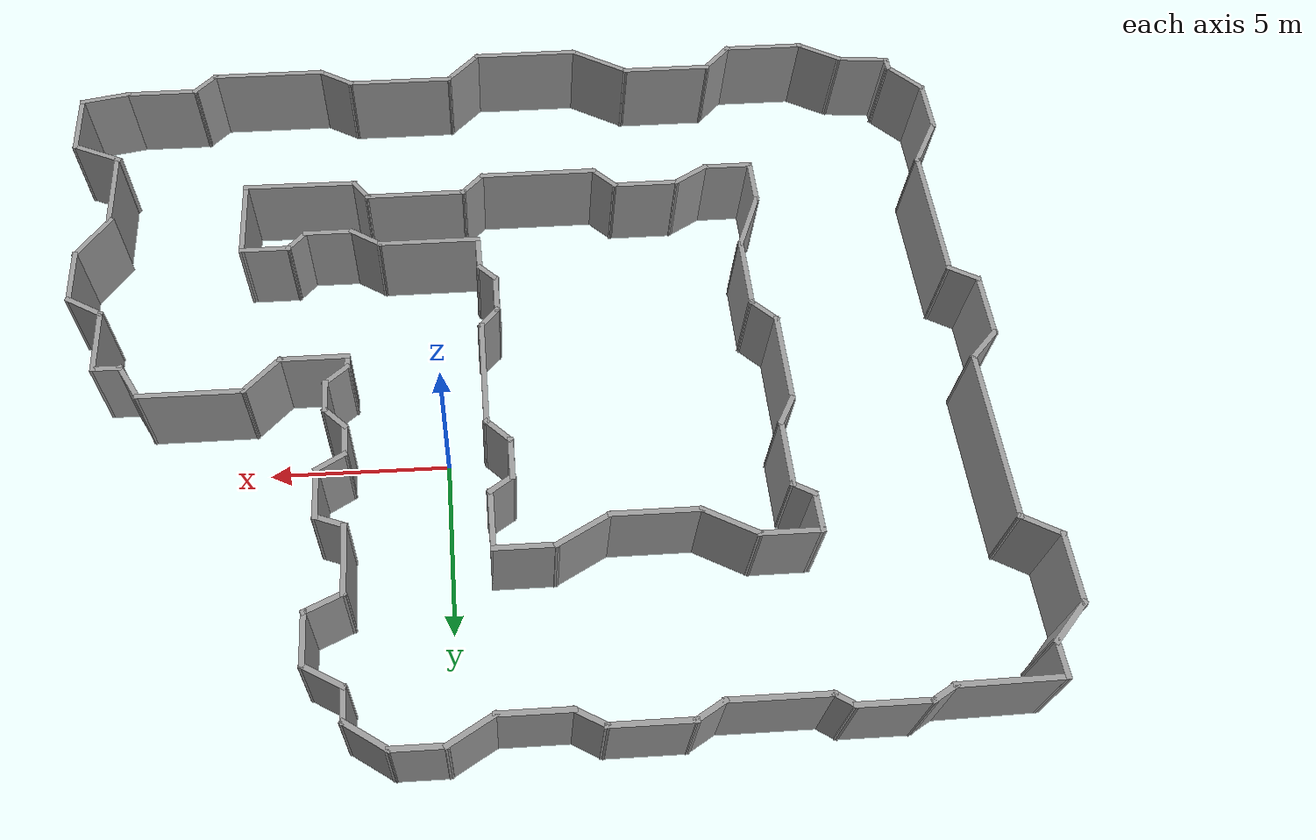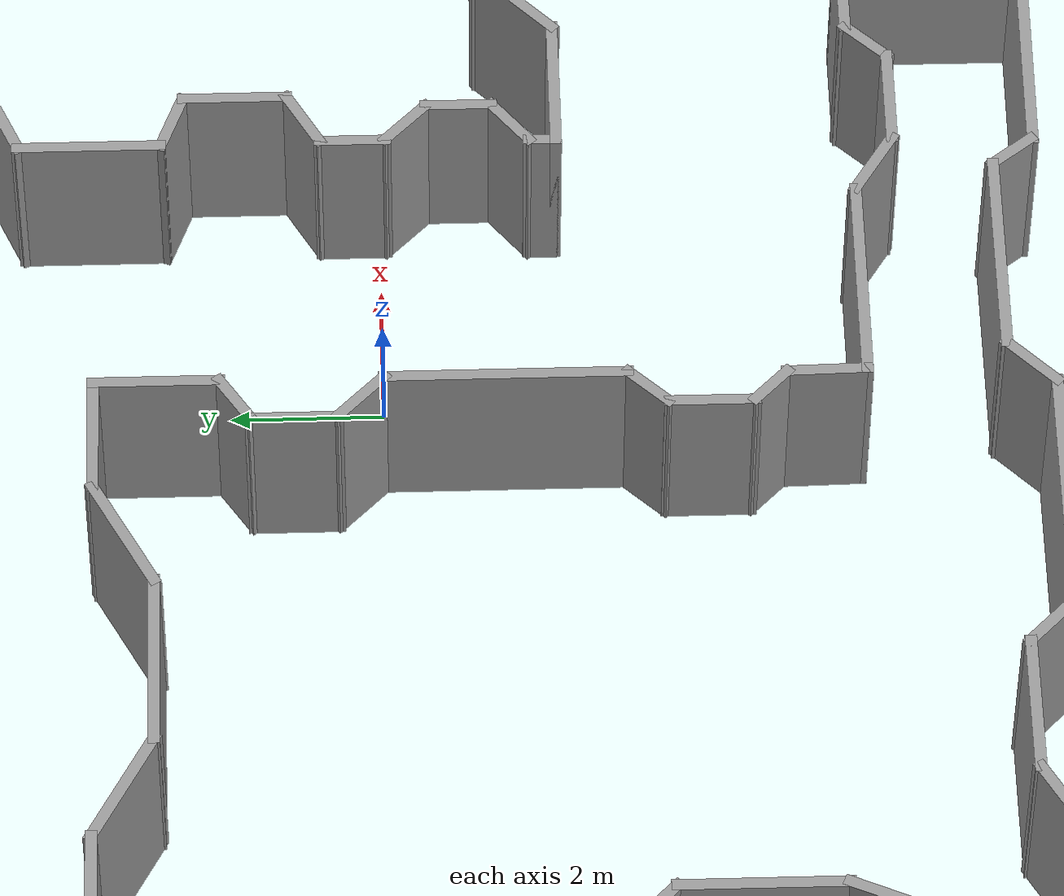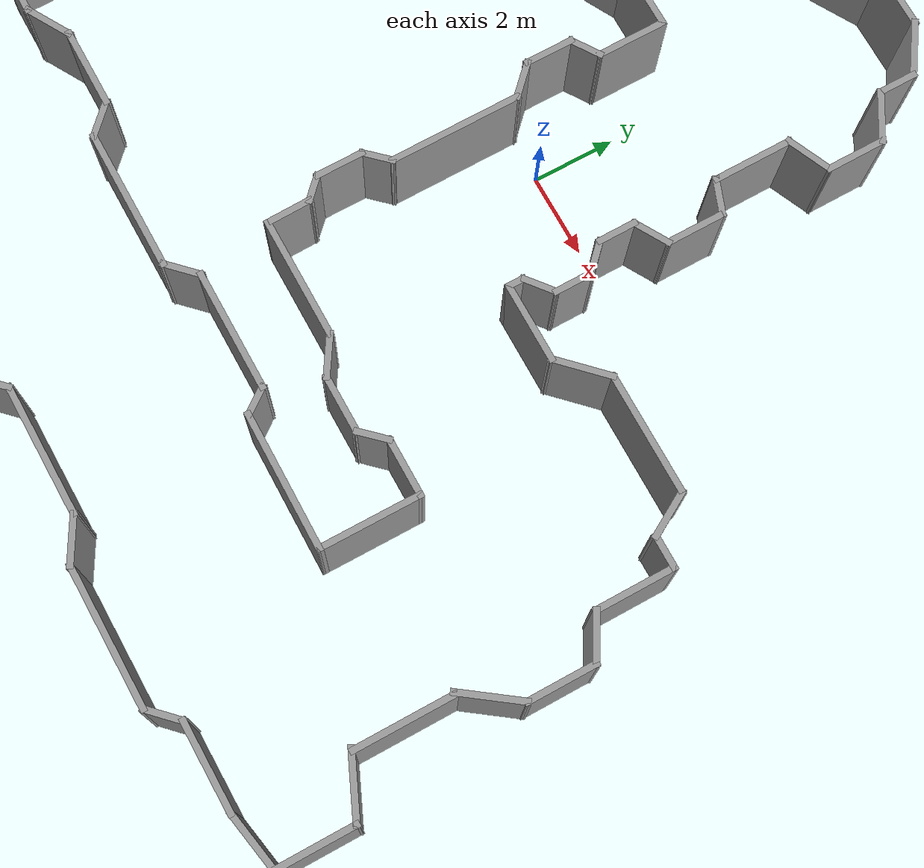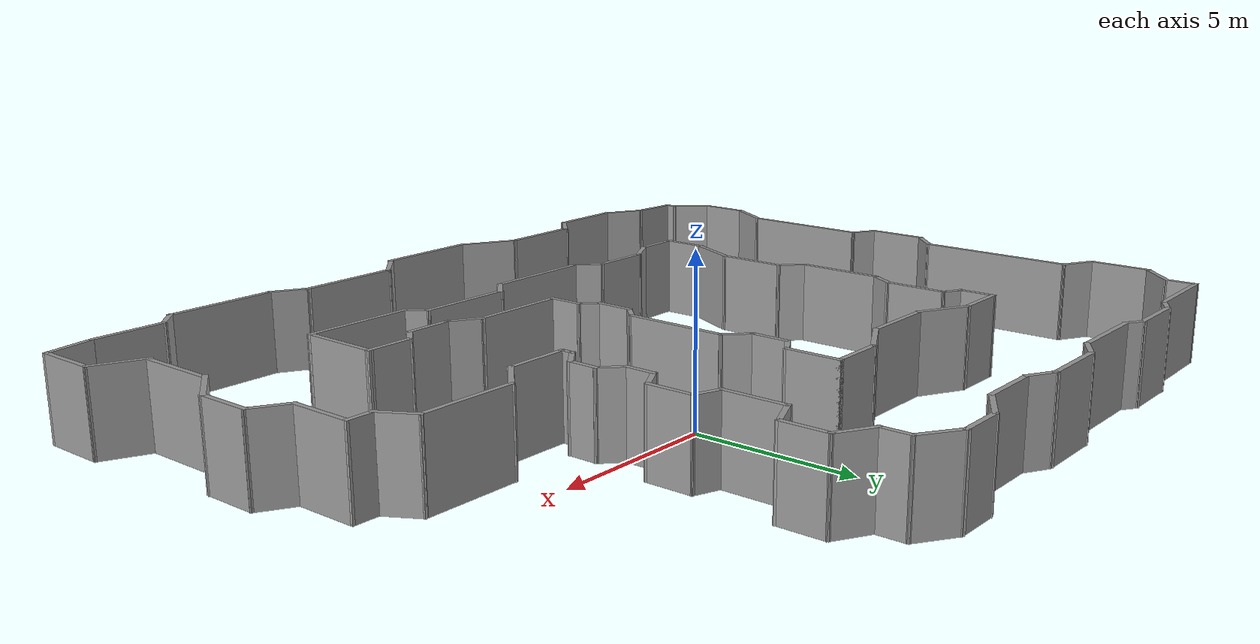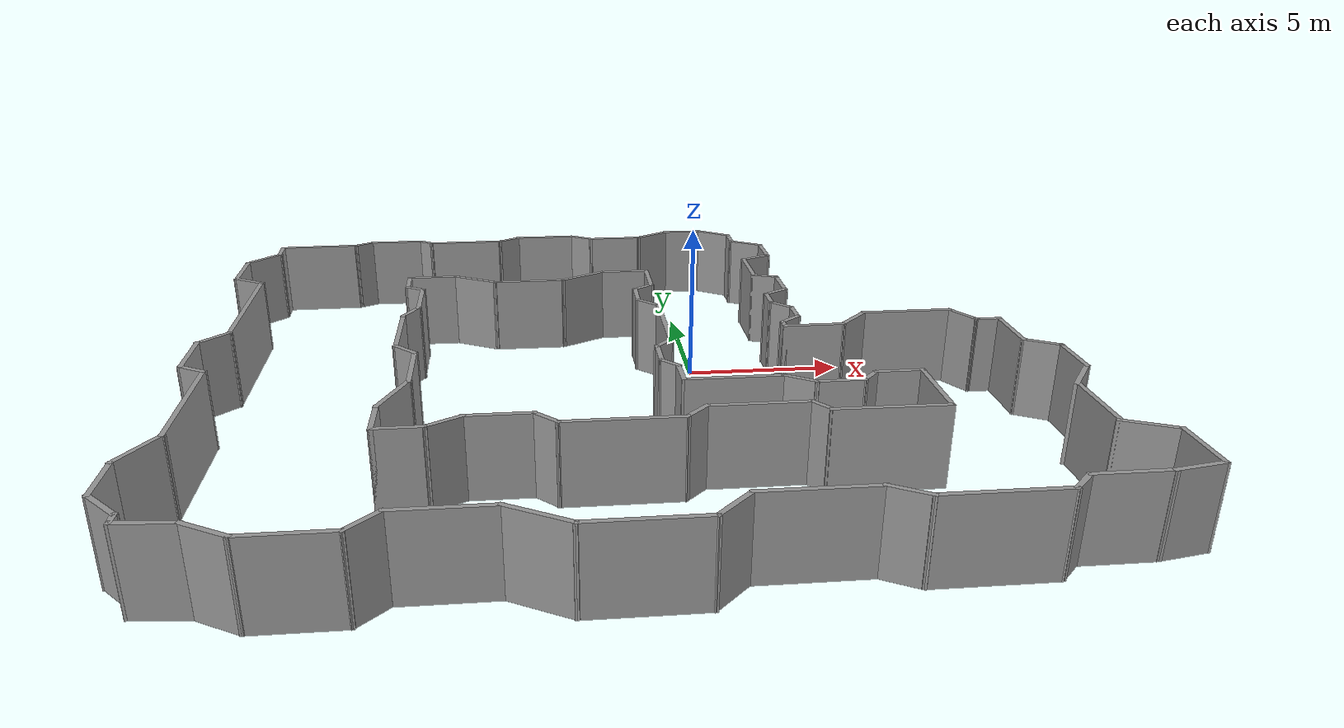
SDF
<?xml version='1.0'?>
<sdf version='1.6'>
  <model name='custom_hallway'>
    <pose frame=''>-2.26322 -2.49916 0 0 -0 0</pose>
    <link name='Wall_100'>
      <collision name='Wall_100_Collision'>
        <geometry>
          <box>
            <size>1 0.15 2.5</size>
          </box>
        </geometry>
        <pose frame=''>0 0 1.25 0 -0 0</pose>
      </collision>
      <visual name='Wall_100_Visual'>
        <pose frame=''>0 0 1.25 0 -0 0</pose>
        <geometry>
          <box>
            <size>1 0.15 2.5</size>
          </box>
        </geometry>
        <material>
          <script>
            <uri>file://media/materials/scripts/gazebo.material</uri>
            <name>Gazebo/Grey</name>
          </script>
          <ambient>1 1 1 1</ambient>
        </material>
      </visual>
      <pose frame=''>-6.80933 -0.6273 0 0 0 -0.785398</pose>
    </link>
    <link name='Wall_101'>
      <collision name='Wall_101_Collision'>
        <geometry>
          <box>
            <size>2.25 0.15 2.5</size>
          </box>
        </geometry>
        <pose frame=''>0 0 1.25 0 -0 0</pose>
      </collision>
      <visual name='Wall_101_Visual'>
        <pose frame=''>0 0 1.25 0 -0 0</pose>
        <geometry>
          <box>
            <size>2.25 0.15 2.5</size>
          </box>
        </geometry>
        <material>
          <script>
            <uri>file://media/materials/scripts/gazebo.material</uri>
            <name>Gazebo/Grey</name>
          </script>
          <ambient>1 1 1 1</ambient>
        </material>
      </visual>
      <pose frame=''>-6.50882 -1.97782 0 0 0 -1.5708</pose>
    </link>
    <link name='Wall_102'>
      <collision name='Wall_102_Collision'>
        <geometry>
          <box>
            <size>1.92514 0.15 2.5</size>
          </box>
        </geometry>
        <pose frame=''>0 0 1.25 0 -0 0</pose>
      </collision>
      <visual name='Wall_102_Visual'>
        <pose frame=''>0 0 1.25 0 -0 0</pose>
        <geometry>
          <box>
            <size>1.92514 0.15 2.5</size>
          </box>
        </geometry>
        <material>
          <script>
            <uri>file://media/materials/scripts/gazebo.material</uri>
            <name>Gazebo/Grey</name>
          </script>
          <ambient>1 1 1 1</ambient>
        </material>
      </visual>
      <pose frame=''>-6.86481 -3.84087 0 0 0 -1.98351</pose>
    </link>
    <link name='Wall_103'>
      <collision name='Wall_103_Collision'>
        <geometry>
          <box>
            <size>1.5 0.15 2.5</size>
          </box>
        </geometry>
        <pose frame=''>0 0 1.25 0 -0 0</pose>
      </collision>
      <visual name='Wall_103_Visual'>
        <pose frame=''>0 0 1.25 0 -0 0</pose>
        <geometry>
          <box>
            <size>1.5 0.15 2.5</size>
          </box>
        </geometry>
        <material>
          <script>
            <uri>file://media/materials/scripts/gazebo.material</uri>
            <name>Gazebo/Grey</name>
          </script>
          <ambient>1 1 1 1</ambient>
        </material>
      </visual>
      <pose frame=''>-7.22081 -5.32891 0 0 0 -1.5708</pose>
    </link>
    <link name='Wall_105'>
      <collision name='Wall_105_Collision'>
        <geometry>
          <box>
            <size>1.02334 0.15 2.5</size>
          </box>
        </geometry>
        <pose frame=''>0 0 1.25 0 -0 0</pose>
      </collision>
      <visual name='Wall_105_Visual'>
        <pose frame=''>0 0 1.25 0 -0 0</pose>
        <geometry>
          <box>
            <size>1.02334 0.15 2.5</size>
          </box>
        </geometry>
        <material>
          <script>
            <uri>file://media/materials/scripts/gazebo.material</uri>
            <name>Gazebo/Grey</name>
          </script>
          <ambient>1 1 1 1</ambient>
        </material>
      </visual>
      <pose frame=''>-12.3267 9.91914 0 0 0 -1.54263</pose>
    </link>
    <link name='Wall_107'>
      <collision name='Wall_107_Collision'>
        <geometry>
          <box>
            <size>0.5 0.15 2.5</size>
          </box>
        </geometry>
        <pose frame=''>0 0 1.25 0 -0 0</pose>
      </collision>
      <visual name='Wall_107_Visual'>
        <pose frame=''>0 0 1.25 0 -0 0</pose>
        <geometry>
          <box>
            <size>0.5 0.15 2.5</size>
          </box>
        </geometry>
        <material>
          <script>
            <uri>file://media/materials/scripts/gazebo.material</uri>
            <name>Gazebo/Grey</name>
          </script>
          <ambient>1 1 1 1</ambient>
        </material>
      </visual>
      <pose frame=''>-12.2855 -9.9614 0 0 -0 1.5708</pose>
    </link>
    <link name='Wall_109'>
      <collision name='Wall_109_Collision'>
        <geometry>
          <box>
            <size>1.18687 0.15 2.5</size>
          </box>
        </geometry>
        <pose frame=''>0 0 1.25 0 -0 0</pose>
      </collision>
      <visual name='Wall_109_Visual'>
        <pose frame=''>0 0 1.25 0 -0 0</pose>
        <geometry>
          <box>
            <size>1.18687 0.15 2.5</size>
          </box>
        </geometry>
        <material>
          <script>
            <uri>file://media/materials/scripts/gazebo.material</uri>
            <name>Gazebo/Grey</name>
          </script>
          <ambient>1 1 1 1</ambient>
        </material>
      </visual>
      <pose frame=''>-7.21264 5.67772 0 0 0 -1.55503</pose>
    </link>
    <link name='Wall_111'>
      <collision name='Wall_111_Collision'>
        <geometry>
          <box>
            <size>1.5 0.15 2.5</size>
          </box>
        </geometry>
        <pose frame=''>0 0 1.25 0 -0 0</pose>
      </collision>
      <visual name='Wall_111_Visual'>
        <pose frame=''>0 0 1.25 0 -0 0</pose>
        <geometry>
          <box>
            <size>1.5 0.15 2.5</size>
          </box>
        </geometry>
        <material>
          <script>
            <uri>file://media/materials/scripts/gazebo.material</uri>
            <name>Gazebo/Grey</name>
          </script>
          <ambient>1 1 1 1</ambient>
        </material>
      </visual>
      <pose frame=''>-6.54581 -6.00391 0 0 -0 0</pose>
    </link>
    <link name='Wall_112'>
      <collision name='Wall_112_Collision'>
        <geometry>
          <box>
            <size>1.25 0.15 2.5</size>
          </box>
        </geometry>
        <pose frame=''>0 0 1.25 0 -0 0</pose>
      </collision>
      <visual name='Wall_112_Visual'>
        <pose frame=''>0 0 1.25 0 -0 0</pose>
        <geometry>
          <box>
            <size>1.25 0.15 2.5</size>
          </box>
        </geometry>
        <material>
          <script>
            <uri>file://media/materials/scripts/gazebo.material</uri>
            <name>Gazebo/Grey</name>
          </script>
          <ambient>1 1 1 1</ambient>
        </material>
      </visual>
      <pose frame=''>-5.3945 -5.72891 0 0 -0 0.523599</pose>
    </link>
    <link name='Wall_113'>
      <collision name='Wall_113_Collision'>
        <geometry>
          <box>
            <size>2 0.15 2.5</size>
          </box>
        </geometry>
        <pose frame=''>0 0 1.25 0 -0 0</pose>
      </collision>
      <visual name='Wall_113_Visual'>
        <pose frame=''>0 0 1.25 0 -0 0</pose>
        <geometry>
          <box>
            <size>2 0.15 2.5</size>
          </box>
        </geometry>
        <material>
          <script>
            <uri>file://media/materials/scripts/gazebo.material</uri>
            <name>Gazebo/Grey</name>
          </script>
          <ambient>1 1 1 1</ambient>
        </material>
      </visual>
      <pose frame=''>-3.99318 -5.45391 0 0 -0 0</pose>
    </link>
    <link name='Wall_114'>
      <collision name='Wall_114_Collision'>
        <geometry>
          <box>
            <size>1 0.15 2.5</size>
          </box>
        </geometry>
        <pose frame=''>0 0 1.25 0 -0 0</pose>
      </collision>
      <visual name='Wall_114_Visual'>
        <pose frame=''>0 0 1.25 0 -0 0</pose>
        <geometry>
          <box>
            <size>1 0.15 2.5</size>
          </box>
        </geometry>
        <material>
          <script>
            <uri>file://media/materials/scripts/gazebo.material</uri>
            <name>Gazebo/Grey</name>
          </script>
          <ambient>1 1 1 1</ambient>
        </material>
      </visual>
      <pose frame=''>-2.76767 -5.75443 0 0 0 -0.785398</pose>
    </link>
    <link name='Wall_115'>
      <collision name='Wall_115_Collision'>
        <geometry>
          <box>
            <size>3.5 0.15 2.5</size>
          </box>
        </geometry>
        <pose frame=''>0 0 1.25 0 -0 0</pose>
      </collision>
      <visual name='Wall_115_Visual'>
        <pose frame=''>0 0 1.25 0 -0 0</pose>
        <geometry>
          <box>
            <size>3.5 0.15 2.5</size>
          </box>
        </geometry>
        <material>
          <script>
            <uri>file://media/materials/scripts/gazebo.material</uri>
            <name>Gazebo/Grey</name>
          </script>
          <ambient>1 1 1 1</ambient>
        </material>
      </visual>
      <pose frame=''>-0.792145 -6.05495 0 0 -0 0</pose>
    </link>
    <link name='Wall_116'>
      <collision name='Wall_116_Collision'>
        <geometry>
          <box>
            <size>1 0.15 2.5</size>
          </box>
        </geometry>
        <pose frame=''>0 0 1.25 0 -0 0</pose>
      </collision>
      <visual name='Wall_116_Visual'>
        <pose frame=''>0 0 1.25 0 -0 0</pose>
        <geometry>
          <box>
            <size>1 0.15 2.5</size>
          </box>
        </geometry>
        <material>
          <script>
            <uri>file://media/materials/scripts/gazebo.material</uri>
            <name>Gazebo/Grey</name>
          </script>
          <ambient>1 1 1 1</ambient>
        </material>
      </visual>
      <pose frame=''>1.18338 -5.75443 0 0 -0 0.785398</pose>
    </link>
    <link name='Wall_117'>
      <collision name='Wall_117_Collision'>
        <geometry>
          <box>
            <size>3 0.15 2.5</size>
          </box>
        </geometry>
        <pose frame=''>0 0 1.25 0 -0 0</pose>
      </collision>
      <visual name='Wall_117_Visual'>
        <pose frame=''>0 0 1.25 0 -0 0</pose>
        <geometry>
          <box>
            <size>3 0.15 2.5</size>
          </box>
        </geometry>
        <material>
          <script>
            <uri>file://media/materials/scripts/gazebo.material</uri>
            <name>Gazebo/Grey</name>
          </script>
          <ambient>1 1 1 1</ambient>
        </material>
      </visual>
      <pose frame=''>2.9089 -5.45391 0 0 -0 0</pose>
    </link>
    <link name='Wall_118'>
      <collision name='Wall_118_Collision'>
        <geometry>
          <box>
            <size>0.80121 0.15 2.5</size>
          </box>
        </geometry>
        <pose frame=''>0 0 1.25 0 -0 0</pose>
      </collision>
      <visual name='Wall_118_Visual'>
        <pose frame=''>0 0 1.25 0 -0 0</pose>
        <geometry>
          <box>
            <size>0.80121 0.15 2.5</size>
          </box>
        </geometry>
        <material>
          <script>
            <uri>file://media/materials/scripts/gazebo.material</uri>
            <name>Gazebo/Grey</name>
          </script>
          <ambient>1 1 1 1</ambient>
        </material>
      </visual>
      <pose frame=''>4.53016 -5.71372 0 0 0 -0.923842</pose>
    </link>
    <link name='Wall_119'>
      <collision name='Wall_119_Collision'>
        <geometry>
          <box>
            <size>3.39543 0.15 2.5</size>
          </box>
        </geometry>
        <pose frame=''>0 0 1.25 0 -0 0</pose>
      </collision>
      <visual name='Wall_119_Visual'>
        <pose frame=''>0 0 1.25 0 -0 0</pose>
        <geometry>
          <box>
            <size>3.39543 0.15 2.5</size>
          </box>
        </geometry>
        <material>
          <script>
            <uri>file://media/materials/scripts/gazebo.material</uri>
            <name>Gazebo/Grey</name>
          </script>
          <ambient>1 1 1 1</ambient>
        </material>
      </visual>
      <pose frame=''>6.34906 -6.01185 0 0 0 -0.009362</pose>
    </link>
    <link name='Wall_121'>
      <collision name='Wall_121_Collision'>
        <geometry>
          <box>
            <size>2 0.15 2.5</size>
          </box>
        </geometry>
        <pose frame=''>0 0 1.25 0 -0 0</pose>
      </collision>
      <visual name='Wall_121_Visual'>
        <pose frame=''>0 0 1.25 0 -0 0</pose>
        <geometry>
          <box>
            <size>2 0.15 2.5</size>
          </box>
        </geometry>
        <material>
          <script>
            <uri>file://media/materials/scripts/gazebo.material</uri>
            <name>Gazebo/Grey</name>
          </script>
          <ambient>1 1 1 1</ambient>
        </material>
      </visual>
      <pose frame=''>5.80419 0.196087 0 0 -0 0</pose>
    </link>
    <link name='Wall_122'>
      <collision name='Wall_122_Collision'>
        <geometry>
          <box>
            <size>1.5 0.15 2.5</size>
          </box>
        </geometry>
        <pose frame=''>0 0 1.25 0 -0 0</pose>
      </collision>
      <visual name='Wall_122_Visual'>
        <pose frame=''>0 0 1.25 0 -0 0</pose>
        <geometry>
          <box>
            <size>1.5 0.15 2.5</size>
          </box>
        </geometry>
        <material>
          <script>
            <uri>file://media/materials/scripts/gazebo.material</uri>
            <name>Gazebo/Grey</name>
          </script>
          <ambient>1 1 1 1</ambient>
        </material>
      </visual>
      <pose frame=''>7.20648 0.673385 0 0 -0 0.785398</pose>
    </link>
    <link name='Wall_123'>
      <collision name='Wall_123_Collision'>
        <geometry>
          <box>
            <size>3 0.15 2.5</size>
          </box>
        </geometry>
        <pose frame=''>0 0 1.25 0 -0 0</pose>
      </collision>
      <visual name='Wall_123_Visual'>
        <pose frame=''>0 0 1.25 0 -0 0</pose>
        <geometry>
          <box>
            <size>3 0.15 2.5</size>
          </box>
        </geometry>
        <material>
          <script>
            <uri>file://media/materials/scripts/gazebo.material</uri>
            <name>Gazebo/Grey</name>
          </script>
          <ambient>1 1 1 1</ambient>
        </material>
      </visual>
      <pose frame=''>9.10878 1.15068 0 0 -0 0</pose>
    </link>
    <link name='Wall_124'>
      <collision name='Wall_124_Collision'>
        <geometry>
          <box>
            <size>1.25 0.15 2.5</size>
          </box>
        </geometry>
        <pose frame=''>0 0 1.25 0 -0 0</pose>
      </collision>
      <visual name='Wall_124_Visual'>
        <pose frame=''>0 0 1.25 0 -0 0</pose>
        <geometry>
          <box>
            <size>1.25 0.15 2.5</size>
          </box>
        </geometry>
        <material>
          <script>
            <uri>file://media/materials/scripts/gazebo.material</uri>
            <name>Gazebo/Grey</name>
          </script>
          <ambient>1 1 1 1</ambient>
        </material>
      </visual>
      <pose frame=''>10.8088 0.674368 0 0 0 -1.0472</pose>
    </link>
    <link name='Wall_125'>
      <collision name='Wall_125_Collision'>
        <geometry>
          <box>
            <size>0.895408 0.15 2.5</size>
          </box>
        </geometry>
        <pose frame=''>0 0 1.25 0 -0 0</pose>
      </collision>
      <visual name='Wall_125_Visual'>
        <pose frame=''>0 0 1.25 0 -0 0</pose>
        <geometry>
          <box>
            <size>0.895408 0.15 2.5</size>
          </box>
        </geometry>
        <material>
          <script>
            <uri>file://media/materials/scripts/gazebo.material</uri>
            <name>Gazebo/Grey</name>
          </script>
          <ambient>1 1 1 1</ambient>
        </material>
      </visual>
      <pose frame=''>11.4565 0.197071 0 0 0 -0.002638</pose>
    </link>
    <link name='Wall_126'>
      <collision name='Wall_126_Collision'>
        <geometry>
          <box>
            <size>2 0.15 2.5</size>
          </box>
        </geometry>
        <pose frame=''>0 0 1.25 0 -0 0</pose>
      </collision>
      <visual name='Wall_126_Visual'>
        <pose frame=''>0 0 1.25 0 -0 0</pose>
        <geometry>
          <box>
            <size>2 0.15 2.5</size>
          </box>
        </geometry>
        <material>
          <script>
            <uri>file://media/materials/scripts/gazebo.material</uri>
            <name>Gazebo/Grey</name>
          </script>
          <ambient>1 1 1 1</ambient>
        </material>
      </visual>
      <pose frame=''>11.8292 -0.728913 0 0 0 -1.5708</pose>
    </link>
    <link name='Wall_127'>
      <collision name='Wall_127_Collision'>
        <geometry>
          <box>
            <size>1.25 0.15 2.5</size>
          </box>
        </geometry>
        <pose frame=''>0 0 1.25 0 -0 0</pose>
      </collision>
      <visual name='Wall_127_Visual'>
        <pose frame=''>0 0 1.25 0 -0 0</pose>
        <geometry>
          <box>
            <size>1.25 0.15 2.5</size>
          </box>
        </geometry>
        <material>
          <script>
            <uri>file://media/materials/scripts/gazebo.material</uri>
            <name>Gazebo/Grey</name>
          </script>
          <ambient>1 1 1 1</ambient>
        </material>
      </visual>
      <pose frame=''>12.3055 -1.92891 0 0 0 -0.523599</pose>
    </link>
    <link name='Wall_128'>
      <collision name='Wall_128_Collision'>
        <geometry>
          <box>
            <size>1.75 0.15 2.5</size>
          </box>
        </geometry>
        <pose frame=''>0 0 1.25 0 -0 0</pose>
      </collision>
      <visual name='Wall_128_Visual'>
        <pose frame=''>0 0 1.25 0 -0 0</pose>
        <geometry>
          <box>
            <size>1.75 0.15 2.5</size>
          </box>
        </geometry>
        <material>
          <script>
            <uri>file://media/materials/scripts/gazebo.material</uri>
            <name>Gazebo/Grey</name>
          </script>
          <ambient>1 1 1 1</ambient>
        </material>
      </visual>
      <pose frame=''>12.7818 -3.00391 0 0 0 -1.5708</pose>
    </link>
    <link name='Wall_129'>
      <collision name='Wall_129_Collision'>
        <geometry>
          <box>
            <size>1.66168 0.15 2.5</size>
          </box>
        </geometry>
        <pose frame=''>0 0 1.25 0 -0 0</pose>
      </collision>
      <visual name='Wall_129_Visual'>
        <pose frame=''>0 0 1.25 0 -0 0</pose>
        <geometry>
          <box>
            <size>1.66168 0.15 2.5</size>
          </box>
        </geometry>
        <material>
          <script>
            <uri>file://media/materials/scripts/gazebo.material</uri>
            <name>Gazebo/Grey</name>
          </script>
          <ambient>1 1 1 1</ambient>
        </material>
      </visual>
      <pose frame=''>12.3373 -4.41523 0 0 0 -2.1995</pose>
    </link>
    <link name='Wall_130'>
      <collision name='Wall_130_Collision'>
        <geometry>
          <box>
            <size>2.5 0.15 2.5</size>
          </box>
        </geometry>
        <pose frame=''>0 0 1.25 0 -0 0</pose>
      </collision>
      <visual name='Wall_130_Visual'>
        <pose frame=''>0 0 1.25 0 -0 0</pose>
        <geometry>
          <box>
            <size>2.5 0.15 2.5</size>
          </box>
        </geometry>
        <material>
          <script>
            <uri>file://media/materials/scripts/gazebo.material</uri>
            <name>Gazebo/Grey</name>
          </script>
          <ambient>1 1 1 1</ambient>
        </material>
      </visual>
      <pose frame=''>11.9463 -6.20155 0 0 0 -1.5708</pose>
    </link>
    <link name='Wall_131'>
      <collision name='Wall_131_Collision'>
        <geometry>
          <box>
            <size>1.66636 0.15 2.5</size>
          </box>
        </geometry>
        <pose frame=''>0 0 1.25 0 -0 0</pose>
      </collision>
      <visual name='Wall_131_Visual'>
        <pose frame=''>0 0 1.25 0 -0 0</pose>
        <geometry>
          <box>
            <size>1.66636 0.15 2.5</size>
          </box>
        </geometry>
        <material>
          <script>
            <uri>file://media/materials/scripts/gazebo.material</uri>
            <name>Gazebo/Grey</name>
          </script>
          <ambient>1 1 1 1</ambient>
        </material>
      </visual>
      <pose frame=''>12.5844 -7.6873 0 0 0 -0.422302</pose>
    </link>
    <link name='Wall_132'>
      <collision name='Wall_132_Collision'>
        <geometry>
          <box>
            <size>2 0.15 2.5</size>
          </box>
        </geometry>
        <pose frame=''>0 0 1.25 0 -0 0</pose>
      </collision>
      <visual name='Wall_132_Visual'>
        <pose frame=''>0 0 1.25 0 -0 0</pose>
        <geometry>
          <box>
            <size>2 0.15 2.5</size>
          </box>
        </geometry>
        <material>
          <script>
            <uri>file://media/materials/scripts/gazebo.material</uri>
            <name>Gazebo/Grey</name>
          </script>
          <ambient>1 1 1 1</ambient>
        </material>
      </visual>
      <pose frame=''>13.2759 -8.92305 0 0 0 -1.5708</pose>
    </link>
    <link name='Wall_133'>
      <collision name='Wall_133_Collision'>
        <geometry>
          <box>
            <size>1.56859 0.15 2.5</size>
          </box>
        </geometry>
        <pose frame=''>0 0 1.25 0 -0 0</pose>
      </collision>
      <visual name='Wall_133_Visual'>
        <pose frame=''>0 0 1.25 0 -0 0</pose>
        <geometry>
          <box>
            <size>1.56859 0.15 2.5</size>
          </box>
        </geometry>
        <material>
          <script>
            <uri>file://media/materials/scripts/gazebo.material</uri>
            <name>Gazebo/Grey</name>
          </script>
          <ambient>1 1 1 1</ambient>
        </material>
      </visual>
      <pose frame=''>12.5776 -9.97199 0 0 0 -2.96594</pose>
    </link>
    <link name='Wall_134'>
      <collision name='Wall_134_Collision'>
        <geometry>
          <box>
            <size>2.25 0.15 2.5</size>
          </box>
        </geometry>
        <pose frame=''>0 0 1.25 0 -0 0</pose>
      </collision>
      <visual name='Wall_134_Visual'>
        <pose frame=''>0 0 1.25 0 -0 0</pose>
        <geometry>
          <box>
            <size>2.25 0.15 2.5</size>
          </box>
        </geometry>
        <material>
          <script>
            <uri>file://media/materials/scripts/gazebo.material</uri>
            <name>Gazebo/Grey</name>
          </script>
          <ambient>1 1 1 1</ambient>
        </material>
      </visual>
      <pose frame=''>10.8292 -10.0959 0 0 -0 3.14159</pose>
    </link>
    <link name='Wall_135'>
      <collision name='Wall_135_Collision'>
        <geometry>
          <box>
            <size>1 0.15 2.5</size>
          </box>
        </geometry>
        <pose frame=''>0 0 1.25 0 -0 0</pose>
      </collision>
      <visual name='Wall_135_Visual'>
        <pose frame=''>0 0 1.25 0 -0 0</pose>
        <geometry>
          <box>
            <size>1 0.15 2.5</size>
          </box>
        </geometry>
        <material>
          <script>
            <uri>file://media/materials/scripts/gazebo.material</uri>
            <name>Gazebo/Grey</name>
          </script>
          <ambient>1 1 1 1</ambient>
        </material>
      </visual>
      <pose frame=''>9.47867 -10.3965 0 0 0 -2.35619</pose>
    </link>
    <link name='Wall_136'>
      <collision name='Wall_136_Collision'>
        <geometry>
          <box>
            <size>3.5 0.15 2.5</size>
          </box>
        </geometry>
        <pose frame=''>0 0 1.25 0 -0 0</pose>
      </collision>
      <visual name='Wall_136_Visual'>
        <pose frame=''>0 0 1.25 0 -0 0</pose>
        <geometry>
          <box>
            <size>3.5 0.15 2.5</size>
          </box>
        </geometry>
        <material>
          <script>
            <uri>file://media/materials/scripts/gazebo.material</uri>
            <name>Gazebo/Grey</name>
          </script>
          <ambient>1 1 1 1</ambient>
        </material>
      </visual>
      <pose frame=''>7.50315 -10.697 0 0 -0 3.14159</pose>
    </link>
    <link name='Wall_137'>
      <collision name='Wall_137_Collision'>
        <geometry>
          <box>
            <size>1.25 0.15 2.5</size>
          </box>
        </geometry>
        <pose frame=''>0 0 1.25 0 -0 0</pose>
      </collision>
      <visual name='Wall_137_Visual'>
        <pose frame=''>0 0 1.25 0 -0 0</pose>
        <geometry>
          <box>
            <size>1.25 0.15 2.5</size>
          </box>
        </geometry>
        <material>
          <script>
            <uri>file://media/materials/scripts/gazebo.material</uri>
            <name>Gazebo/Grey</name>
          </script>
          <ambient>1 1 1 1</ambient>
        </material>
      </visual>
      <pose frame=''>5.35183 -10.422 0 0 -0 2.61799</pose>
    </link>
    <link name='Wall_138'>
      <collision name='Wall_138_Collision'>
        <geometry>
          <box>
            <size>3.25 0.15 2.5</size>
          </box>
        </geometry>
        <pose frame=''>0 0 1.25 0 -0 0</pose>
      </collision>
      <visual name='Wall_138_Visual'>
        <pose frame=''>0 0 1.25 0 -0 0</pose>
        <geometry>
          <box>
            <size>3.25 0.15 2.5</size>
          </box>
        </geometry>
        <material>
          <script>
            <uri>file://media/materials/scripts/gazebo.material</uri>
            <name>Gazebo/Grey</name>
          </script>
          <ambient>1 1 1 1</ambient>
        </material>
      </visual>
      <pose frame=''>3.32552 -10.147 0 0 -0 3.14159</pose>
    </link>
    <link name='Wall_139'>
      <collision name='Wall_139_Collision'>
        <geometry>
          <box>
            <size>1.5 0.15 2.5</size>
          </box>
        </geometry>
        <pose frame=''>0 0 1.25 0 -0 0</pose>
      </collision>
      <visual name='Wall_139_Visual'>
        <pose frame=''>0 0 1.25 0 -0 0</pose>
        <geometry>
          <box>
            <size>1.5 0.15 2.5</size>
          </box>
        </geometry>
        <material>
          <script>
            <uri>file://media/materials/scripts/gazebo.material</uri>
            <name>Gazebo/Grey</name>
          </script>
          <ambient>1 1 1 1</ambient>
        </material>
      </visual>
      <pose frame=''>1.29822 -10.6243 0 0 0 -2.35619</pose>
    </link>
    <link name='Wall_140'>
      <collision name='Wall_140_Collision'>
        <geometry>
          <box>
            <size>3.25 0.15 2.5</size>
          </box>
        </geometry>
        <pose frame=''>0 0 1.25 0 -0 0</pose>
      </collision>
      <visual name='Wall_140_Visual'>
        <pose frame=''>0 0 1.25 0 -0 0</pose>
        <geometry>
          <box>
            <size>3.25 0.15 2.5</size>
          </box>
        </geometry>
        <material>
          <script>
            <uri>file://media/materials/scripts/gazebo.material</uri>
            <name>Gazebo/Grey</name>
          </script>
          <ambient>1 1 1 1</ambient>
        </material>
      </visual>
      <pose frame=''>-0.729076 -11.1016 0 0 -0 3.14159</pose>
    </link>
    <link name='Wall_141'>
      <collision name='Wall_141_Collision'>
        <geometry>
          <box>
            <size>2 0.15 2.5</size>
          </box>
        </geometry>
        <pose frame=''>0 0 1.25 0 -0 0</pose>
      </collision>
      <visual name='Wall_141_Visual'>
        <pose frame=''>0 0 1.25 0 -0 0</pose>
        <geometry>
          <box>
            <size>2 0.15 2.5</size>
          </box>
        </geometry>
        <material>
          <script>
            <uri>file://media/materials/scripts/gazebo.material</uri>
            <name>Gazebo/Grey</name>
          </script>
          <ambient>1 1 1 1</ambient>
        </material>
      </visual>
      <pose frame=''>-3.08015 -10.6391 0 0 -0 2.61799</pose>
    </link>
    <link name='Wall_142'>
      <collision name='Wall_142_Collision'>
        <geometry>
          <box>
            <size>2.75 0.15 2.5</size>
          </box>
        </geometry>
        <pose frame=''>0 0 1.25 0 -0 0</pose>
      </collision>
      <visual name='Wall_142_Visual'>
        <pose frame=''>0 0 1.25 0 -0 0</pose>
        <geometry>
          <box>
            <size>2.75 0.15 2.5</size>
          </box>
        </geometry>
        <material>
          <script>
            <uri>file://media/materials/scripts/gazebo.material</uri>
            <name>Gazebo/Grey</name>
          </script>
          <ambient>1 1 1 1</ambient>
        </material>
      </visual>
      <pose frame=''>-5.18122 -10.1766 0 0 -0 3.14159</pose>
    </link>
    <link name='Wall_143'>
      <collision name='Wall_143_Collision'>
        <geometry>
          <box>
            <size>1.25 0.15 2.5</size>
          </box>
        </geometry>
        <pose frame=''>0 0 1.25 0 -0 0</pose>
      </collision>
      <visual name='Wall_143_Visual'>
        <pose frame=''>0 0 1.25 0 -0 0</pose>
        <geometry>
          <box>
            <size>1.25 0.15 2.5</size>
          </box>
        </geometry>
        <material>
          <script>
            <uri>file://media/materials/scripts/gazebo.material</uri>
            <name>Gazebo/Grey</name>
          </script>
          <ambient>1 1 1 1</ambient>
        </material>
      </visual>
      <pose frame=''>-6.87013 -10.5655 0 0 0 -2.35619</pose>
    </link>
    <link name='Wall_144'>
      <collision name='Wall_144_Collision'>
        <geometry>
          <box>
            <size>2.5 0.15 2.5</size>
          </box>
        </geometry>
        <pose frame=''>0 0 1.25 0 -0 0</pose>
      </collision>
      <visual name='Wall_144_Visual'>
        <pose frame=''>0 0 1.25 0 -0 0</pose>
        <geometry>
          <box>
            <size>2.5 0.15 2.5</size>
          </box>
        </geometry>
        <material>
          <script>
            <uri>file://media/materials/scripts/gazebo.material</uri>
            <name>Gazebo/Grey</name>
          </script>
          <ambient>1 1 1 1</ambient>
        </material>
      </visual>
      <pose frame=''>-8.43404 -10.9544 0 0 -0 3.14159</pose>
    </link>
    <link name='Wall_145'>
      <collision name='Wall_145_Collision'>
        <geometry>
          <box>
            <size>1.5 0.15 2.5</size>
          </box>
        </geometry>
        <pose frame=''>0 0 1.25 0 -0 0</pose>
      </collision>
      <visual name='Wall_145_Visual'>
        <pose frame=''>0 0 1.25 0 -0 0</pose>
        <geometry>
          <box>
            <size>1.5 0.15 2.5</size>
          </box>
        </geometry>
        <material>
          <script>
            <uri>file://media/materials/scripts/gazebo.material</uri>
            <name>Gazebo/Grey</name>
          </script>
          <ambient>1 1 1 1</ambient>
        </material>
      </visual>
      <pose frame=''>-10.1936 -10.6169 0 0 -0 2.61799</pose>
    </link>
    <link name='Wall_147'>
      <collision name='Wall_147_Collision'>
        <geometry>
          <box>
            <size>1.66413 0.15 2.5</size>
          </box>
        </geometry>
        <pose frame=''>0 0 1.25 0 -0 0</pose>
      </collision>
      <visual name='Wall_147_Visual'>
        <pose frame=''>0 0 1.25 0 -0 0</pose>
        <geometry>
          <box>
            <size>1.66413 0.15 2.5</size>
          </box>
        </geometry>
        <material>
          <script>
            <uri>file://media/materials/scripts/gazebo.material</uri>
            <name>Gazebo/Grey</name>
          </script>
          <ambient>1 1 1 1</ambient>
        </material>
      </visual>
      <pose frame=''>-11.5319 -10.2079 0 0 -0 3.04701</pose>
    </link>
    <link name='Wall_21'>
      <collision name='Wall_21_Collision'>
        <geometry>
          <box>
            <size>0.859757 0.15 2.5</size>
          </box>
        </geometry>
        <pose frame=''>0 0 1.25 0 -0 0</pose>
      </collision>
      <visual name='Wall_21_Visual'>
        <pose frame=''>0 0 1.25 0 -0 0</pose>
        <geometry>
          <box>
            <size>0.859757 0.15 2.5</size>
          </box>
        </geometry>
        <material>
          <script>
            <uri>file://media/materials/scripts/gazebo.material</uri>
            <name>Gazebo/Grey</name>
          </script>
          <ambient>1 1 1 1</ambient>
        </material>
      </visual>
      <pose frame=''>6.38603 -3.9124 0 0 0 -2.32565</pose>
    </link>
    <link name='Wall_22'>
      <collision name='Wall_22_Collision'>
        <geometry>
          <box>
            <size>1.5 0.15 2.5</size>
          </box>
        </geometry>
        <pose frame=''>0 0 1.25 0 -0 0</pose>
      </collision>
      <visual name='Wall_22_Visual'>
        <pose frame=''>0 0 1.25 0 -0 0</pose>
        <geometry>
          <box>
            <size>1.5 0.15 2.5</size>
          </box>
        </geometry>
        <material>
          <script>
            <uri>file://media/materials/scripts/gazebo.material</uri>
            <name>Gazebo/Grey</name>
          </script>
          <ambient>1 1 1 1</ambient>
        </material>
      </visual>
      <pose frame=''>5.46788 -4.17088 0 0 -0 3.14159</pose>
    </link>
    <link name='Wall_23'>
      <collision name='Wall_23_Collision'>
        <geometry>
          <box>
            <size>1.11403 0.15 2.5</size>
          </box>
        </geometry>
        <pose frame=''>0 0 1.25 0 -0 0</pose>
      </collision>
      <visual name='Wall_23_Visual'>
        <pose frame=''>0 0 1.25 0 -0 0</pose>
        <geometry>
          <box>
            <size>1.11403 0.15 2.5</size>
          </box>
        </geometry>
        <material>
          <script>
            <uri>file://media/materials/scripts/gazebo.material</uri>
            <name>Gazebo/Grey</name>
          </script>
          <ambient>1 1 1 1</ambient>
        </material>
      </visual>
      <pose frame=''>4.38603 -3.9124 0 0 -0 2.57559</pose>
    </link>
    <link name='Wall_25'>
      <collision name='Wall_25_Collision'>
        <geometry>
          <box>
            <size>3 0.15 2.5</size>
          </box>
        </geometry>
        <pose frame=''>0 0 1.25 0 -0 0</pose>
      </collision>
      <visual name='Wall_25_Visual'>
        <pose frame=''>0 0 1.25 0 -0 0</pose>
        <geometry>
          <box>
            <size>3 0.15 2.5</size>
          </box>
        </geometry>
        <material>
          <script>
            <uri>file://media/materials/scripts/gazebo.material</uri>
            <name>Gazebo/Grey</name>
          </script>
          <ambient>1 1 1 1</ambient>
        </material>
      </visual>
      <pose frame=''>2.55419 -3.65391 0 0 -0 0</pose>
    </link>
    <link name='Wall_27'>
      <collision name='Wall_27_Collision'>
        <geometry>
          <box>
            <size>1.5 0.15 2.5</size>
          </box>
        </geometry>
        <pose frame=''>0 0 1.25 0 -0 0</pose>
      </collision>
      <visual name='Wall_27_Visual'>
        <pose frame=''>0 0 1.25 0 -0 0</pose>
        <geometry>
          <box>
            <size>1.5 0.15 2.5</size>
          </box>
        </geometry>
        <material>
          <script>
            <uri>file://media/materials/scripts/gazebo.material</uri>
            <name>Gazebo/Grey</name>
          </script>
          <ambient>1 1 1 1</ambient>
        </material>
      </visual>
      <pose frame=''>7.30419 -3.65391 0 0 -0 0</pose>
    </link>
    <link name='Wall_29'>
      <collision name='Wall_29_Collision'>
        <geometry>
          <box>
            <size>0.75 0.15 2.5</size>
          </box>
        </geometry>
        <pose frame=''>0 0 1.25 0 -0 0</pose>
      </collision>
      <visual name='Wall_29_Visual'>
        <pose frame=''>0 0 1.25 0 -0 0</pose>
        <geometry>
          <box>
            <size>0.75 0.15 2.5</size>
          </box>
        </geometry>
        <material>
          <script>
            <uri>file://media/materials/scripts/gazebo.material</uri>
            <name>Gazebo/Grey</name>
          </script>
          <ambient>1 1 1 1</ambient>
        </material>
      </visual>
      <pose frame=''>0.895053 -2.42058 0 0 -0 2.35619</pose>
    </link>
    <link name='Wall_30'>
      <collision name='Wall_30_Collision'>
        <geometry>
          <box>
            <size>1.23479 0.15 2.5</size>
          </box>
        </geometry>
        <pose frame=''>0 0 1.25 0 -0 0</pose>
      </collision>
      <visual name='Wall_30_Visual'>
        <pose frame=''>0 0 1.25 0 -0 0</pose>
        <geometry>
          <box>
            <size>1.23479 0.15 2.5</size>
          </box>
        </geometry>
        <material>
          <script>
            <uri>file://media/materials/scripts/gazebo.material</uri>
            <name>Gazebo/Grey</name>
          </script>
          <ambient>1 1 1 1</ambient>
        </material>
      </visual>
      <pose frame=''>0.682921 -1.66606 0 0 -0 1.5708</pose>
    </link>
    <link name='Wall_31'>
      <collision name='Wall_31_Collision'>
        <geometry>
          <box>
            <size>0.83969 0.15 2.5</size>
          </box>
        </geometry>
        <pose frame=''>0 0 1.25 0 -0 0</pose>
      </collision>
      <visual name='Wall_31_Visual'>
        <pose frame=''>0 0 1.25 0 -0 0</pose>
        <geometry>
          <box>
            <size>0.83969 0.15 2.5</size>
          </box>
        </geometry>
        <material>
          <script>
            <uri>file://media/materials/scripts/gazebo.material</uri>
            <name>Gazebo/Grey</name>
          </script>
          <ambient>1 1 1 1</ambient>
        </material>
      </visual>
      <pose frame=''>0.918189 -0.856327 0 0 -0 0.81997</pose>
    </link>
    <link name='Wall_33'>
      <collision name='Wall_33_Collision'>
        <geometry>
          <box>
            <size>1.17143 0.15 2.5</size>
          </box>
        </geometry>
        <pose frame=''>0 0 1.25 0 -0 0</pose>
      </collision>
      <visual name='Wall_33_Visual'>
        <pose frame=''>0 0 1.25 0 -0 0</pose>
        <geometry>
          <box>
            <size>1.17143 0.15 2.5</size>
          </box>
        </geometry>
        <material>
          <script>
            <uri>file://media/materials/scripts/gazebo.material</uri>
            <name>Gazebo/Grey</name>
          </script>
          <ambient>1 1 1 1</ambient>
        </material>
      </visual>
      <pose frame=''>1.11819 -3.14331 0 0 -0 1.59234</pose>
    </link>
    <link name='Wall_35'>
      <collision name='Wall_35_Collision'>
        <geometry>
          <box>
            <size>0.870502 0.15 2.5</size>
          </box>
        </geometry>
        <pose frame=''>0 0 1.25 0 -0 0</pose>
      </collision>
      <visual name='Wall_35_Visual'>
        <pose frame=''>0 0 1.25 0 -0 0</pose>
        <geometry>
          <box>
            <size>0.870502 0.15 2.5</size>
          </box>
        </geometry>
        <material>
          <script>
            <uri>file://media/materials/scripts/gazebo.material</uri>
            <name>Gazebo/Grey</name>
          </script>
          <ambient>1 1 1 1</ambient>
        </material>
      </visual>
      <pose frame=''>0.852302 4.39646 0 0 0 -2.55428</pose>
    </link>
    <link name='Wall_36'>
      <collision name='Wall_36_Collision'>
        <geometry>
          <box>
            <size>1.25 0.15 2.5</size>
          </box>
        </geometry>
        <pose frame=''>0 0 1.25 0 -0 0</pose>
      </collision>
      <visual name='Wall_36_Visual'>
        <pose frame=''>0 0 1.25 0 -0 0</pose>
        <geometry>
          <box>
            <size>1.25 0.15 2.5</size>
          </box>
        </geometry>
        <material>
          <script>
            <uri>file://media/materials/scripts/gazebo.material</uri>
            <name>Gazebo/Grey</name>
          </script>
          <ambient>1 1 1 1</ambient>
        </material>
      </visual>
      <pose frame=''>0.552417 3.64684 0 0 0 -1.5708</pose>
    </link>
    <link name='Wall_37'>
      <collision name='Wall_37_Collision'>
        <geometry>
          <box>
            <size>1 0.15 2.5</size>
          </box>
        </geometry>
        <pose frame=''>0 0 1.25 0 -0 0</pose>
      </collision>
      <visual name='Wall_37_Visual'>
        <pose frame=''>0 0 1.25 0 -0 0</pose>
        <geometry>
          <box>
            <size>1 0.15 2.5</size>
          </box>
        </geometry>
        <material>
          <script>
            <uri>file://media/materials/scripts/gazebo.material</uri>
            <name>Gazebo/Grey</name>
          </script>
          <ambient>1 1 1 1</ambient>
        </material>
      </visual>
      <pose frame=''>0.852937 2.79632 0 0 0 -0.785398</pose>
    </link>
    <link name='Wall_39'>
      <collision name='Wall_39_Collision'>
        <geometry>
          <box>
            <size>1.75 0.15 2.5</size>
          </box>
        </geometry>
        <pose frame=''>0 0 1.25 0 -0 0</pose>
      </collision>
      <visual name='Wall_39_Visual'>
        <pose frame=''>0 0 1.25 0 -0 0</pose>
        <geometry>
          <box>
            <size>1.75 0.15 2.5</size>
          </box>
        </geometry>
        <material>
          <script>
            <uri>file://media/materials/scripts/gazebo.material</uri>
            <name>Gazebo/Grey</name>
          </script>
          <ambient>1 1 1 1</ambient>
        </material>
      </visual>
      <pose frame=''>1.15219 5.39609 0 0 -0 1.5708</pose>
    </link>
    <link name='Wall_41'>
      <collision name='Wall_41_Collision'>
        <geometry>
          <box>
            <size>3.25 0.15 2.5</size>
          </box>
        </geometry>
        <pose frame=''>0 0 1.25 0 -0 0</pose>
      </collision>
      <visual name='Wall_41_Visual'>
        <pose frame=''>0 0 1.25 0 -0 0</pose>
        <geometry>
          <box>
            <size>3.25 0.15 2.5</size>
          </box>
        </geometry>
        <material>
          <script>
            <uri>file://media/materials/scripts/gazebo.material</uri>
            <name>Gazebo/Grey</name>
          </script>
          <ambient>1 1 1 1</ambient>
        </material>
      </visual>
      <pose frame=''>1.15346 0.945798 0 0 0 -1.5708</pose>
    </link>
    <link name='Wall_43'>
      <collision name='Wall_43_Collision'>
        <geometry>
          <box>
            <size>0.910309 0.15 2.5</size>
          </box>
        </geometry>
        <pose frame=''>0 0 1.25 0 -0 0</pose>
      </collision>
      <visual name='Wall_43_Visual'>
        <pose frame=''>0 0 1.25 0 -0 0</pose>
        <geometry>
          <box>
            <size>0.910309 0.15 2.5</size>
          </box>
        </geometry>
        <material>
          <script>
            <uri>file://media/materials/scripts/gazebo.material</uri>
            <name>Gazebo/Grey</name>
          </script>
          <ambient>1 1 1 1</ambient>
        </material>
      </visual>
      <pose frame=''>5.17462 0.785332 0 0 -0 0.680696</pose>
    </link>
    <link name='Wall_44'>
      <collision name='Wall_44_Collision'>
        <geometry>
          <box>
            <size>1 0.15 2.5</size>
          </box>
        </geometry>
        <pose frame=''>0 0 1.25 0 -0 0</pose>
      </collision>
      <visual name='Wall_44_Visual'>
        <pose frame=''>0 0 1.25 0 -0 0</pose>
        <geometry>
          <box>
            <size>1 0.15 2.5</size>
          </box>
        </geometry>
        <material>
          <script>
            <uri>file://media/materials/scripts/gazebo.material</uri>
            <name>Gazebo/Grey</name>
          </script>
          <ambient>1 1 1 1</ambient>
        </material>
      </visual>
      <pose frame=''>5.47005 1.44958 0 0 -0 1.5708</pose>
    </link>
    <link name='Wall_45'>
      <collision name='Wall_45_Collision'>
        <geometry>
          <box>
            <size>0.9181 0.15 2.5</size>
          </box>
        </geometry>
        <pose frame=''>0 0 1.25 0 -0 0</pose>
      </collision>
      <visual name='Wall_45_Visual'>
        <pose frame=''>0 0 1.25 0 -0 0</pose>
        <geometry>
          <box>
            <size>0.9181 0.15 2.5</size>
          </box>
        </geometry>
        <material>
          <script>
            <uri>file://media/materials/scripts/gazebo.material</uri>
            <name>Gazebo/Grey</name>
          </script>
          <ambient>1 1 1 1</ambient>
        </material>
      </visual>
      <pose frame=''>5.19745 2.1451 0 0 -0 2.36001</pose>
    </link>
    <link name='Wall_47'>
      <collision name='Wall_47_Collision'>
        <geometry>
          <box>
            <size>1 0.15 2.5</size>
          </box>
        </geometry>
        <pose frame=''>0 0 1.25 0 -0 0</pose>
      </collision>
      <visual name='Wall_47_Visual'>
        <pose frame=''>0 0 1.25 0 -0 0</pose>
        <geometry>
          <box>
            <size>1 0.15 2.5</size>
          </box>
        </geometry>
        <material>
          <script>
            <uri>file://media/materials/scripts/gazebo.material</uri>
            <name>Gazebo/Grey</name>
          </script>
          <ambient>1 1 1 1</ambient>
        </material>
      </visual>
      <pose frame=''>5.29291 3.47813 0 0 -0 0.523599</pose>
    </link>
    <link name='Wall_48'>
      <collision name='Wall_48_Collision'>
        <geometry>
          <box>
            <size>1.5 0.15 2.5</size>
          </box>
        </geometry>
        <pose frame=''>0 0 1.25 0 -0 0</pose>
      </collision>
      <visual name='Wall_48_Visual'>
        <pose frame=''>0 0 1.25 0 -0 0</pose>
        <geometry>
          <box>
            <size>1.5 0.15 2.5</size>
          </box>
        </geometry>
        <material>
          <script>
            <uri>file://media/materials/scripts/gazebo.material</uri>
            <name>Gazebo/Grey</name>
          </script>
          <ambient>1 1 1 1</ambient>
        </material>
      </visual>
      <pose frame=''>5.66097 4.36563 0 0 -0 1.5708</pose>
    </link>
    <link name='Wall_49'>
      <collision name='Wall_49_Collision'>
        <geometry>
          <box>
            <size>0.963959 0.15 2.5</size>
          </box>
        </geometry>
        <pose frame=''>0 0 1.25 0 -0 0</pose>
      </collision>
      <visual name='Wall_49_Visual'>
        <pose frame=''>0 0 1.25 0 -0 0</pose>
        <geometry>
          <box>
            <size>0.963959 0.15 2.5</size>
          </box>
        </geometry>
        <material>
          <script>
            <uri>file://media/materials/scripts/gazebo.material</uri>
            <name>Gazebo/Grey</name>
          </script>
          <ambient>1 1 1 1</ambient>
        </material>
      </visual>
      <pose frame=''>5.28042 5.18488 0 0 -0 2.77928</pose>
    </link>
    <link name='Wall_50'>
      <collision name='Wall_50_Collision'>
        <geometry>
          <box>
            <size>2 0.15 2.5</size>
          </box>
        </geometry>
        <pose frame=''>0 0 1.25 0 -0 0</pose>
      </collision>
      <visual name='Wall_50_Visual'>
        <pose frame=''>0 0 1.25 0 -0 0</pose>
        <geometry>
          <box>
            <size>2 0.15 2.5</size>
          </box>
        </geometry>
        <material>
          <script>
            <uri>file://media/materials/scripts/gazebo.material</uri>
            <name>Gazebo/Grey</name>
          </script>
          <ambient>1 1 1 1</ambient>
        </material>
      </visual>
      <pose frame=''>4.91136 6.26563 0 0 -0 1.5708</pose>
    </link>
    <link name='Wall_51'>
      <collision name='Wall_51_Collision'>
        <geometry>
          <box>
            <size>1.22064 0.15 2.5</size>
          </box>
        </geometry>
        <pose frame=''>0 0 1.25 0 -0 0</pose>
      </collision>
      <visual name='Wall_51_Visual'>
        <pose frame=''>0 0 1.25 0 -0 0</pose>
        <geometry>
          <box>
            <size>1.22064 0.15 2.5</size>
          </box>
        </geometry>
        <material>
          <script>
            <uri>file://media/materials/scripts/gazebo.material</uri>
            <name>Gazebo/Grey</name>
          </script>
          <ambient>1 1 1 1</ambient>
        </material>
      </visual>
      <pose frame=''>5.38867 7.39738 0 0 -0 0.419933</pose>
    </link>
    <link name='Wall_52'>
      <collision name='Wall_52_Collision'>
        <geometry>
          <box>
            <size>1.5 0.15 2.5</size>
          </box>
        </geometry>
        <pose frame=''>0 0 1.25 0 -0 0</pose>
      </collision>
      <visual name='Wall_52_Visual'>
        <pose frame=''>0 0 1.25 0 -0 0</pose>
        <geometry>
          <box>
            <size>1.5 0.15 2.5</size>
          </box>
        </geometry>
        <material>
          <script>
            <uri>file://media/materials/scripts/gazebo.material</uri>
            <name>Gazebo/Grey</name>
          </script>
          <ambient>1 1 1 1</ambient>
        </material>
      </visual>
      <pose frame=''>5.87748 8.29063 0 0 -0 1.5708</pose>
    </link>
    <link name='Wall_53'>
      <collision name='Wall_53_Collision'>
        <geometry>
          <box>
            <size>1.30478 0.15 2.5</size>
          </box>
        </geometry>
        <pose frame=''>0 0 1.25 0 -0 0</pose>
      </collision>
      <visual name='Wall_53_Visual'>
        <pose frame=''>0 0 1.25 0 -0 0</pose>
        <geometry>
          <box>
            <size>1.30478 0.15 2.5</size>
          </box>
        </geometry>
        <material>
          <script>
            <uri>file://media/materials/scripts/gazebo.material</uri>
            <name>Gazebo/Grey</name>
          </script>
          <ambient>1 1 1 1</ambient>
        </material>
      </visual>
      <pose frame=''>5.37833 9.25586 0 0 -0 2.61492</pose>
    </link>
    <link name='Wall_54'>
      <collision name='Wall_54_Collision'>
        <geometry>
          <box>
            <size>1 0.15 2.5</size>
          </box>
        </geometry>
        <pose frame=''>0 0 1.25 0 -0 0</pose>
      </collision>
      <visual name='Wall_54_Visual'>
        <pose frame=''>0 0 1.25 0 -0 0</pose>
        <geometry>
          <box>
            <size>1 0.15 2.5</size>
          </box>
        </geometry>
        <material>
          <script>
            <uri>file://media/materials/scripts/gazebo.material</uri>
            <name>Gazebo/Grey</name>
          </script>
          <ambient>1 1 1 1</ambient>
        </material>
      </visual>
      <pose frame=''>4.87919 9.97109 0 0 -0 1.5708</pose>
    </link>
    <link name='Wall_56'>
      <collision name='Wall_56_Collision'>
        <geometry>
          <box>
            <size>0.5 0.15 2.5</size>
          </box>
        </geometry>
        <pose frame=''>0 0 1.25 0 -0 0</pose>
      </collision>
      <visual name='Wall_56_Visual'>
        <pose frame=''>0 0 1.25 0 -0 0</pose>
        <geometry>
          <box>
            <size>0.5 0.15 2.5</size>
          </box>
        </geometry>
        <material>
          <script>
            <uri>file://media/materials/scripts/gazebo.material</uri>
            <name>Gazebo/Grey</name>
          </script>
          <ambient>1 1 1 1</ambient>
        </material>
      </visual>
      <pose frame=''>4.87919 0.371087 0 0 -0 1.5708</pose>
    </link>
    <link name='Wall_58'>
      <collision name='Wall_58_Collision'>
        <geometry>
          <box>
            <size>1 0.15 2.5</size>
          </box>
        </geometry>
        <pose frame=''>0 0 1.25 0 -0 0</pose>
      </collision>
      <visual name='Wall_58_Visual'>
        <pose frame=''>0 0 1.25 0 -0 0</pose>
        <geometry>
          <box>
            <size>1 0.15 2.5</size>
          </box>
        </geometry>
        <material>
          <script>
            <uri>file://media/materials/scripts/gazebo.material</uri>
            <name>Gazebo/Grey</name>
          </script>
          <ambient>1 1 1 1</ambient>
        </material>
      </visual>
      <pose frame=''>4.92485 2.84063 0 0 -0 1.5708</pose>
    </link>
    <link name='Wall_60'>
      <collision name='Wall_60_Collision'>
        <geometry>
          <box>
            <size>1.77067 0.15 2.5</size>
          </box>
        </geometry>
        <pose frame=''>0 0 1.25 0 -0 0</pose>
      </collision>
      <visual name='Wall_60_Visual'>
        <pose frame=''>0 0 1.25 0 -0 0</pose>
        <geometry>
          <box>
            <size>1.77067 0.15 2.5</size>
          </box>
        </geometry>
        <material>
          <script>
            <uri>file://media/materials/scripts/gazebo.material</uri>
            <name>Gazebo/Grey</name>
          </script>
          <ambient>1 1 1 1</ambient>
        </material>
      </visual>
      <pose frame=''>-1.16099 5.81134 0 0 0 -2.64686</pose>
    </link>
    <link name='Wall_61'>
      <collision name='Wall_61_Collision'>
        <geometry>
          <box>
            <size>2.5 0.15 2.5</size>
          </box>
        </geometry>
        <pose frame=''>0 0 1.25 0 -0 0</pose>
      </collision>
      <visual name='Wall_61_Visual'>
        <pose frame=''>0 0 1.25 0 -0 0</pose>
        <geometry>
          <box>
            <size>2.5 0.15 2.5</size>
          </box>
        </geometry>
        <material>
          <script>
            <uri>file://media/materials/scripts/gazebo.material</uri>
            <name>Gazebo/Grey</name>
          </script>
          <ambient>1 1 1 1</ambient>
        </material>
      </visual>
      <pose frame=''>-3.04916 5.42659 0 0 -0 3.14159</pose>
    </link>
    <link name='Wall_62'>
      <collision name='Wall_62_Collision'>
        <geometry>
          <box>
            <size>1.7446 0.15 2.5</size>
          </box>
        </geometry>
        <pose frame=''>0 0 1.25 0 -0 0</pose>
      </collision>
      <visual name='Wall_62_Visual'>
        <pose frame=''>0 0 1.25 0 -0 0</pose>
        <geometry>
          <box>
            <size>1.7446 0.15 2.5</size>
          </box>
        </geometry>
        <material>
          <script>
            <uri>file://media/materials/scripts/gazebo.material</uri>
            <name>Gazebo/Grey</name>
          </script>
          <ambient>1 1 1 1</ambient>
        </material>
      </visual>
      <pose frame=''>-4.92249 5.81134 0 0 -0 2.63802</pose>
    </link>
    <link name='Wall_64'>
      <collision name='Wall_64_Collision'>
        <geometry>
          <box>
            <size>0.840814 0.15 2.5</size>
          </box>
        </geometry>
        <pose frame=''>0 0 1.25 0 -0 0</pose>
      </collision>
      <visual name='Wall_64_Visual'>
        <pose frame=''>0 0 1.25 0 -0 0</pose>
        <geometry>
          <box>
            <size>0.840814 0.15 2.5</size>
          </box>
        </geometry>
        <material>
          <script>
            <uri>file://media/materials/scripts/gazebo.material</uri>
            <name>Gazebo/Grey</name>
          </script>
          <ambient>1 1 1 1</ambient>
        </material>
      </visual>
      <pose frame=''>-9.31805 10.5623 0 0 -0 0.502149</pose>
    </link>
    <link name='Wall_65'>
      <collision name='Wall_65_Collision'>
        <geometry>
          <box>
            <size>2 0.15 2.5</size>
          </box>
        </geometry>
        <pose frame=''>0 0 1.25 0 -0 0</pose>
      </collision>
      <visual name='Wall_65_Visual'>
        <pose frame=''>0 0 1.25 0 -0 0</pose>
        <geometry>
          <box>
            <size>2 0.15 2.5</size>
          </box>
        </geometry>
        <material>
          <script>
            <uri>file://media/materials/scripts/gazebo.material</uri>
            <name>Gazebo/Grey</name>
          </script>
          <ambient>1 1 1 1</ambient>
        </material>
      </visual>
      <pose frame=''>-8.09028 10.7286 0 0 -0 0</pose>
    </link>
    <link name='Wall_66'>
      <collision name='Wall_66_Collision'>
        <geometry>
          <box>
            <size>0.689098 0.15 2.5</size>
          </box>
        </geometry>
        <pose frame=''>0 0 1.25 0 -0 0</pose>
      </collision>
      <visual name='Wall_66_Visual'>
        <pose frame=''>0 0 1.25 0 -0 0</pose>
        <geometry>
          <box>
            <size>0.689098 0.15 2.5</size>
          </box>
        </geometry>
        <material>
          <script>
            <uri>file://media/materials/scripts/gazebo.material</uri>
            <name>Gazebo/Grey</name>
          </script>
          <ambient>1 1 1 1</ambient>
        </material>
      </visual>
      <pose frame=''>-6.94132 10.5786 0 0 0 -0.590149</pose>
    </link>
    <link name='Wall_68'>
      <collision name='Wall_68_Collision'>
        <geometry>
          <box>
            <size>1 0.15 2.5</size>
          </box>
        </geometry>
        <pose frame=''>0 0 1.25 0 -0 0</pose>
      </collision>
      <visual name='Wall_68_Visual'>
        <pose frame=''>0 0 1.25 0 -0 0</pose>
        <geometry>
          <box>
            <size>1 0.15 2.5</size>
          </box>
        </geometry>
        <material>
          <script>
            <uri>file://media/materials/scripts/gazebo.material</uri>
            <name>Gazebo/Grey</name>
          </script>
          <ambient>1 1 1 1</ambient>
        </material>
      </visual>
      <pose frame=''>-3.74931 10.6411 0 0 -0 0.523599</pose>
    </link>
    <link name='Wall_69'>
      <collision name='Wall_69_Collision'>
        <geometry>
          <box>
            <size>2.25 0.15 2.5</size>
          </box>
        </geometry>
        <pose frame=''>0 0 1.25 0 -0 0</pose>
      </collision>
      <visual name='Wall_69_Visual'>
        <pose frame=''>0 0 1.25 0 -0 0</pose>
        <geometry>
          <box>
            <size>2.25 0.15 2.5</size>
          </box>
        </geometry>
        <material>
          <script>
            <uri>file://media/materials/scripts/gazebo.material</uri>
            <name>Gazebo/Grey</name>
          </script>
          <ambient>1 1 1 1</ambient>
        </material>
      </visual>
      <pose frame=''>-2.33124 10.8536 0 0 -0 0</pose>
    </link>
    <link name='Wall_7'>
      <collision name='Wall_7_Collision'>
        <geometry>
          <box>
            <size>2.50001 0.15 2.5</size>
          </box>
        </geometry>
        <pose frame=''>0 0 1.25 0 -0 0</pose>
      </collision>
      <visual name='Wall_7_Visual'>
        <pose frame=''>0 0 1.25 0 -0 0</pose>
        <geometry>
          <box>
            <size>2.50001 0.15 2.5</size>
          </box>
        </geometry>
        <material>
          <script>
            <uri>file://media/materials/scripts/gazebo.material</uri>
            <name>Gazebo/Grey</name>
          </script>
          <ambient>1 1 1 1</ambient>
        </material>
      </visual>
      <pose frame=''>7.97545 -4.82891 0 0 -0 1.56761</pose>
    </link>
    <link name='Wall_70'>
      <collision name='Wall_70_Collision'>
        <geometry>
          <box>
            <size>1 0.15 2.5</size>
          </box>
        </geometry>
        <pose frame=''>0 0 1.25 0 -0 0</pose>
      </collision>
      <visual name='Wall_70_Visual'>
        <pose frame=''>0 0 1.25 0 -0 0</pose>
        <geometry>
          <box>
            <size>1 0.15 2.5</size>
          </box>
        </geometry>
        <material>
          <script>
            <uri>file://media/materials/scripts/gazebo.material</uri>
            <name>Gazebo/Grey</name>
          </script>
          <ambient>1 1 1 1</ambient>
        </material>
      </visual>
      <pose frame=''>-0.913183 10.6411 0 0 0 -0.523599</pose>
    </link>
    <link name='Wall_71'>
      <collision name='Wall_71_Collision'>
        <geometry>
          <box>
            <size>2 0.15 2.5</size>
          </box>
        </geometry>
        <pose frame=''>0 0 1.25 0 -0 0</pose>
      </collision>
      <visual name='Wall_71_Visual'>
        <pose frame=''>0 0 1.25 0 -0 0</pose>
        <geometry>
          <box>
            <size>2 0.15 2.5</size>
          </box>
        </geometry>
        <material>
          <script>
            <uri>file://media/materials/scripts/gazebo.material</uri>
            <name>Gazebo/Grey</name>
          </script>
          <ambient>1 1 1 1</ambient>
        </material>
      </visual>
      <pose frame=''>0.379877 10.4286 0 0 -0 0</pose>
    </link>
    <link name='Wall_72'>
      <collision name='Wall_72_Collision'>
        <geometry>
          <box>
            <size>1.5 0.15 2.5</size>
          </box>
        </geometry>
        <pose frame=''>0 0 1.25 0 -0 0</pose>
      </collision>
      <visual name='Wall_72_Visual'>
        <pose frame=''>0 0 1.25 0 -0 0</pose>
        <geometry>
          <box>
            <size>1.5 0.15 2.5</size>
          </box>
        </geometry>
        <material>
          <script>
            <uri>file://media/materials/scripts/gazebo.material</uri>
            <name>Gazebo/Grey</name>
          </script>
          <ambient>1 1 1 1</ambient>
        </material>
      </visual>
      <pose frame=''>1.88945 10.7661 0 0 -0 0.523599</pose>
    </link>
    <link name='Wall_73'>
      <collision name='Wall_73_Collision'>
        <geometry>
          <box>
            <size>1.5 0.15 2.5</size>
          </box>
        </geometry>
        <pose frame=''>0 0 1.25 0 -0 0</pose>
      </collision>
      <visual name='Wall_73_Visual'>
        <pose frame=''>0 0 1.25 0 -0 0</pose>
        <geometry>
          <box>
            <size>1.5 0.15 2.5</size>
          </box>
        </geometry>
        <material>
          <script>
            <uri>file://media/materials/scripts/gazebo.material</uri>
            <name>Gazebo/Grey</name>
          </script>
          <ambient>1 1 1 1</ambient>
        </material>
      </visual>
      <pose frame=''>3.14901 11.1036 0 0 -0 0</pose>
    </link>
    <link name='Wall_74'>
      <collision name='Wall_74_Collision'>
        <geometry>
          <box>
            <size>1.42041 0.15 2.5</size>
          </box>
        </geometry>
        <pose frame=''>0 0 1.25 0 -0 0</pose>
      </collision>
      <visual name='Wall_74_Visual'>
        <pose frame=''>0 0 1.25 0 -0 0</pose>
        <geometry>
          <box>
            <size>1.42041 0.15 2.5</size>
          </box>
        </geometry>
        <material>
          <script>
            <uri>file://media/materials/scripts/gazebo.material</uri>
            <name>Gazebo/Grey</name>
          </script>
          <ambient>1 1 1 1</ambient>
        </material>
      </visual>
      <pose frame=''>4.3516 10.7498 0 0 0 -0.590652</pose>
    </link>
    <link name='Wall_76'>
      <collision name='Wall_76_Collision'>
        <geometry>
          <box>
            <size>2.86852 0.15 2.5</size>
          </box>
        </geometry>
        <pose frame=''>0 0 1.25 0 -0 0</pose>
      </collision>
      <visual name='Wall_76_Visual'>
        <pose frame=''>0 0 1.25 0 -0 0</pose>
        <geometry>
          <box>
            <size>2.86852 0.15 2.5</size>
          </box>
        </geometry>
        <material>
          <script>
            <uri>file://media/materials/scripts/gazebo.material</uri>
            <name>Gazebo/Grey</name>
          </script>
          <ambient>1 1 1 1</ambient>
        </material>
      </visual>
      <pose frame=''>-10.9799 10.3759 0 0 -0 0.014882</pose>
    </link>
    <link name='Wall_78'>
      <collision name='Wall_78_Collision'>
        <geometry>
          <box>
            <size>2.75 0.15 2.5</size>
          </box>
        </geometry>
        <pose frame=''>0 0 1.25 0 -0 0</pose>
      </collision>
      <visual name='Wall_78_Visual'>
        <pose frame=''>0 0 1.25 0 -0 0</pose>
        <geometry>
          <box>
            <size>2.75 0.15 2.5</size>
          </box>
        </geometry>
        <material>
          <script>
            <uri>file://media/materials/scripts/gazebo.material</uri>
            <name>Gazebo/Grey</name>
          </script>
          <ambient>1 1 1 1</ambient>
        </material>
      </visual>
      <pose frame=''>-5.41737 10.4286 0 0 -0 0</pose>
    </link>
    <link name='Wall_80'>
      <collision name='Wall_80_Collision'>
        <geometry>
          <box>
            <size>1.75 0.15 2.5</size>
          </box>
        </geometry>
        <pose frame=''>0 0 1.25 0 -0 0</pose>
      </collision>
      <visual name='Wall_80_Visual'>
        <pose frame=''>0 0 1.25 0 -0 0</pose>
        <geometry>
          <box>
            <size>1.75 0.15 2.5</size>
          </box>
        </geometry>
        <material>
          <script>
            <uri>file://media/materials/scripts/gazebo.material</uri>
            <name>Gazebo/Grey</name>
          </script>
          <ambient>1 1 1 1</ambient>
        </material>
      </visual>
      <pose frame=''>-6.42081 6.19609 0 0 -0 0</pose>
    </link>
    <link name='Wall_82'>
      <collision name='Wall_82_Collision'>
        <geometry>
          <box>
            <size>1.75 0.15 2.5</size>
          </box>
        </geometry>
        <pose frame=''>0 0 1.25 0 -0 0</pose>
      </collision>
      <visual name='Wall_82_Visual'>
        <pose frame=''>0 0 1.25 0 -0 0</pose>
        <geometry>
          <box>
            <size>1.75 0.15 2.5</size>
          </box>
        </geometry>
        <material>
          <script>
            <uri>file://media/materials/scripts/gazebo.material</uri>
            <name>Gazebo/Grey</name>
          </script>
          <ambient>1 1 1 1</ambient>
        </material>
      </visual>
      <pose frame=''>0.352187 6.19609 0 0 -0 0</pose>
    </link>
    <link name='Wall_84'>
      <collision name='Wall_84_Collision'>
        <geometry>
          <box>
            <size>1.5 0.15 2.5</size>
          </box>
        </geometry>
        <pose frame=''>0 0 1.25 0 -0 0</pose>
      </collision>
      <visual name='Wall_84_Visual'>
        <pose frame=''>0 0 1.25 0 -0 0</pose>
        <geometry>
          <box>
            <size>1.5 0.15 2.5</size>
          </box>
        </geometry>
        <material>
          <script>
            <uri>file://media/materials/scripts/gazebo.material</uri>
            <name>Gazebo/Grey</name>
          </script>
          <ambient>1 1 1 1</ambient>
        </material>
      </visual>
      <pose frame=''>-12.7917 9.00534 0 0 0 -2.35619</pose>
    </link>
    <link name='Wall_85'>
      <collision name='Wall_85_Collision'>
        <geometry>
          <box>
            <size>2 0.15 2.5</size>
          </box>
        </geometry>
        <pose frame=''>0 0 1.25 0 -0 0</pose>
      </collision>
      <visual name='Wall_85_Visual'>
        <pose frame=''>0 0 1.25 0 -0 0</pose>
        <geometry>
          <box>
            <size>2 0.15 2.5</size>
          </box>
        </geometry>
        <material>
          <script>
            <uri>file://media/materials/scripts/gazebo.material</uri>
            <name>Gazebo/Grey</name>
          </script>
          <ambient>1 1 1 1</ambient>
        </material>
      </visual>
      <pose frame=''>-13.269 7.60304 0 0 0 -1.5708</pose>
    </link>
    <link name='Wall_86'>
      <collision name='Wall_86_Collision'>
        <geometry>
          <box>
            <size>1.25 0.15 2.5</size>
          </box>
        </geometry>
        <pose frame=''>0 0 1.25 0 -0 0</pose>
      </collision>
      <visual name='Wall_86_Visual'>
        <pose frame=''>0 0 1.25 0 -0 0</pose>
        <geometry>
          <box>
            <size>1.25 0.15 2.5</size>
          </box>
        </geometry>
        <material>
          <script>
            <uri>file://media/materials/scripts/gazebo.material</uri>
            <name>Gazebo/Grey</name>
          </script>
          <ambient>1 1 1 1</ambient>
        </material>
      </visual>
      <pose frame=''>-12.7927 6.40304 0 0 0 -0.523599</pose>
    </link>
    <link name='Wall_87'>
      <collision name='Wall_87_Collision'>
        <geometry>
          <box>
            <size>5 0.15 2.5</size>
          </box>
        </geometry>
        <pose frame=''>0 0 1.25 0 -0 0</pose>
      </collision>
      <visual name='Wall_87_Visual'>
        <pose frame=''>0 0 1.25 0 -0 0</pose>
        <geometry>
          <box>
            <size>5 0.15 2.5</size>
          </box>
        </geometry>
        <material>
          <script>
            <uri>file://media/materials/scripts/gazebo.material</uri>
            <name>Gazebo/Grey</name>
          </script>
          <ambient>1 1 1 1</ambient>
        </material>
      </visual>
      <pose frame=''>-12.3164 3.70304 0 0 0 -1.5708</pose>
    </link>
    <link name='Wall_88'>
      <collision name='Wall_88_Collision'>
        <geometry>
          <box>
            <size>1.25 0.15 2.5</size>
          </box>
        </geometry>
        <pose frame=''>0 0 1.25 0 -0 0</pose>
      </collision>
      <visual name='Wall_88_Visual'>
        <pose frame=''>0 0 1.25 0 -0 0</pose>
        <geometry>
          <box>
            <size>1.25 0.15 2.5</size>
          </box>
        </geometry>
        <material>
          <script>
            <uri>file://media/materials/scripts/gazebo.material</uri>
            <name>Gazebo/Grey</name>
          </script>
          <ambient>1 1 1 1</ambient>
        </material>
      </visual>
      <pose frame=''>-12.7053 0.889137 0 0 0 -2.35619</pose>
    </link>
    <link name='Wall_89'>
      <collision name='Wall_89_Collision'>
        <geometry>
          <box>
            <size>2 0.15 2.5</size>
          </box>
        </geometry>
        <pose frame=''>0 0 1.25 0 -0 0</pose>
      </collision>
      <visual name='Wall_89_Visual'>
        <pose frame=''>0 0 1.25 0 -0 0</pose>
        <geometry>
          <box>
            <size>2 0.15 2.5</size>
          </box>
        </geometry>
        <material>
          <script>
            <uri>file://media/materials/scripts/gazebo.material</uri>
            <name>Gazebo/Grey</name>
          </script>
          <ambient>1 1 1 1</ambient>
        </material>
      </visual>
      <pose frame=''>-13.0942 -0.424772 0 0 0 -1.5708</pose>
    </link>
    <link name='Wall_90'>
      <collision name='Wall_90_Collision'>
        <geometry>
          <box>
            <size>1 0.15 2.5</size>
          </box>
        </geometry>
        <pose frame=''>0 0 1.25 0 -0 0</pose>
      </collision>
      <visual name='Wall_90_Visual'>
        <pose frame=''>0 0 1.25 0 -0 0</pose>
        <geometry>
          <box>
            <size>1 0.15 2.5</size>
          </box>
        </geometry>
        <material>
          <script>
            <uri>file://media/materials/scripts/gazebo.material</uri>
            <name>Gazebo/Grey</name>
          </script>
          <ambient>1 1 1 1</ambient>
        </material>
      </visual>
      <pose frame=''>-12.7262 -1.56227 0 0 0 -0.523599</pose>
    </link>
    <link name='Wall_91'>
      <collision name='Wall_91_Collision'>
        <geometry>
          <box>
            <size>4.25 0.15 2.5</size>
          </box>
        </geometry>
        <pose frame=''>0 0 1.25 0 -0 0</pose>
      </collision>
      <visual name='Wall_91_Visual'>
        <pose frame=''>0 0 1.25 0 -0 0</pose>
        <geometry>
          <box>
            <size>4.25 0.15 2.5</size>
          </box>
        </geometry>
        <material>
          <script>
            <uri>file://media/materials/scripts/gazebo.material</uri>
            <name>Gazebo/Grey</name>
          </script>
          <ambient>1 1 1 1</ambient>
        </material>
      </visual>
      <pose frame=''>-12.3581 -3.82477 0 0 0 -1.5708</pose>
    </link>
    <link name='Wall_92'>
      <collision name='Wall_92_Collision'>
        <geometry>
          <box>
            <size>1.75 0.15 2.5</size>
          </box>
        </geometry>
        <pose frame=''>0 0 1.25 0 -0 0</pose>
      </collision>
      <visual name='Wall_92_Visual'>
        <pose frame=''>0 0 1.25 0 -0 0</pose>
        <geometry>
          <box>
            <size>1.75 0.15 2.5</size>
          </box>
        </geometry>
        <material>
          <script>
            <uri>file://media/materials/scripts/gazebo.material</uri>
            <name>Gazebo/Grey</name>
          </script>
          <ambient>1 1 1 1</ambient>
        </material>
      </visual>
      <pose frame=''>-12.7581 -6.56759 0 0 0 -2.0944</pose>
    </link>
    <link name='Wall_93'>
      <collision name='Wall_93_Collision'>
        <geometry>
          <box>
            <size>1.75 0.15 2.5</size>
          </box>
        </geometry>
        <pose frame=''>0 0 1.25 0 -0 0</pose>
      </collision>
      <visual name='Wall_93_Visual'>
        <pose frame=''>0 0 1.25 0 -0 0</pose>
        <geometry>
          <box>
            <size>1.75 0.15 2.5</size>
          </box>
        </geometry>
        <material>
          <script>
            <uri>file://media/materials/scripts/gazebo.material</uri>
            <name>Gazebo/Grey</name>
          </script>
          <ambient>1 1 1 1</ambient>
        </material>
      </visual>
      <pose frame=''>-13.1581 -8.06041 0 0 0 -1.5708</pose>
    </link>
    <link name='Wall_94'>
      <collision name='Wall_94_Collision'>
        <geometry>
          <box>
            <size>1.42233 0.15 2.5</size>
          </box>
        </geometry>
        <pose frame=''>0 0 1.25 0 -0 0</pose>
      </collision>
      <visual name='Wall_94_Visual'>
        <pose frame=''>0 0 1.25 0 -0 0</pose>
        <geometry>
          <box>
            <size>1.42233 0.15 2.5</size>
          </box>
        </geometry>
        <material>
          <script>
            <uri>file://media/materials/scripts/gazebo.material</uri>
            <name>Gazebo/Grey</name>
          </script>
          <ambient>1 1 1 1</ambient>
        </material>
      </visual>
      <pose frame=''>-12.7218 -9.32341 0 0 0 -0.81509</pose>
    </link>
    <link name='Wall_96'>
      <collision name='Wall_96_Collision'>
        <geometry>
          <box>
            <size>0.75 0.15 2.5</size>
          </box>
        </geometry>
        <pose frame=''>0 0 1.25 0 -0 0</pose>
      </collision>
      <visual name='Wall_96_Visual'>
        <pose frame=''>0 0 1.25 0 -0 0</pose>
        <geometry>
          <box>
            <size>0.75 0.15 2.5</size>
          </box>
        </geometry>
        <material>
          <script>
            <uri>file://media/materials/scripts/gazebo.material</uri>
            <name>Gazebo/Grey</name>
          </script>
          <ambient>1 1 1 1</ambient>
        </material>
      </visual>
      <pose frame=''>-6.94466 5.00934 0 0 0 -0.523599</pose>
    </link>
    <link name='Wall_97'>
      <collision name='Wall_97_Collision'>
        <geometry>
          <box>
            <size>2 0.15 2.5</size>
          </box>
        </geometry>
        <pose frame=''>0 0 1.25 0 -0 0</pose>
      </collision>
      <visual name='Wall_97_Visual'>
        <pose frame=''>0 0 1.25 0 -0 0</pose>
        <geometry>
          <box>
            <size>2 0.15 2.5</size>
          </box>
        </geometry>
        <material>
          <script>
            <uri>file://media/materials/scripts/gazebo.material</uri>
            <name>Gazebo/Grey</name>
          </script>
          <ambient>1 1 1 1</ambient>
        </material>
      </visual>
      <pose frame=''>-6.68486 3.93434 0 0 0 -1.5708</pose>
    </link>
    <link name='Wall_98'>
      <collision name='Wall_98_Collision'>
        <geometry>
          <box>
            <size>1 0.15 2.5</size>
          </box>
        </geometry>
        <pose frame=''>0 0 1.25 0 -0 0</pose>
      </collision>
      <visual name='Wall_98_Visual'>
        <pose frame=''>0 0 1.25 0 -0 0</pose>
        <geometry>
          <box>
            <size>1 0.15 2.5</size>
          </box>
        </geometry>
        <material>
          <script>
            <uri>file://media/materials/scripts/gazebo.material</uri>
            <name>Gazebo/Grey</name>
          </script>
          <ambient>1 1 1 1</ambient>
        </material>
      </visual>
      <pose frame=''>-6.89736 2.64128 0 0 0 -2.0944</pose>
    </link>
    <link name='Wall_99'>
      <collision name='Wall_99_Collision'>
        <geometry>
          <box>
            <size>2.75 0.15 2.5</size>
          </box>
        </geometry>
        <pose frame=''>0 0 1.25 0 -0 0</pose>
      </collision>
      <visual name='Wall_99_Visual'>
        <pose frame=''>0 0 1.25 0 -0 0</pose>
        <geometry>
          <box>
            <size>2.75 0.15 2.5</size>
          </box>
        </geometry>
        <material>
          <script>
            <uri>file://media/materials/scripts/gazebo.material</uri>
            <name>Gazebo/Grey</name>
          </script>
          <ambient>1 1 1 1</ambient>
        </material>
      </visual>
      <pose frame=''>-7.10986 0.973221 0 0 0 -1.5708</pose>
    </link>
    <static>1</static>
  </model>
</sdf>
